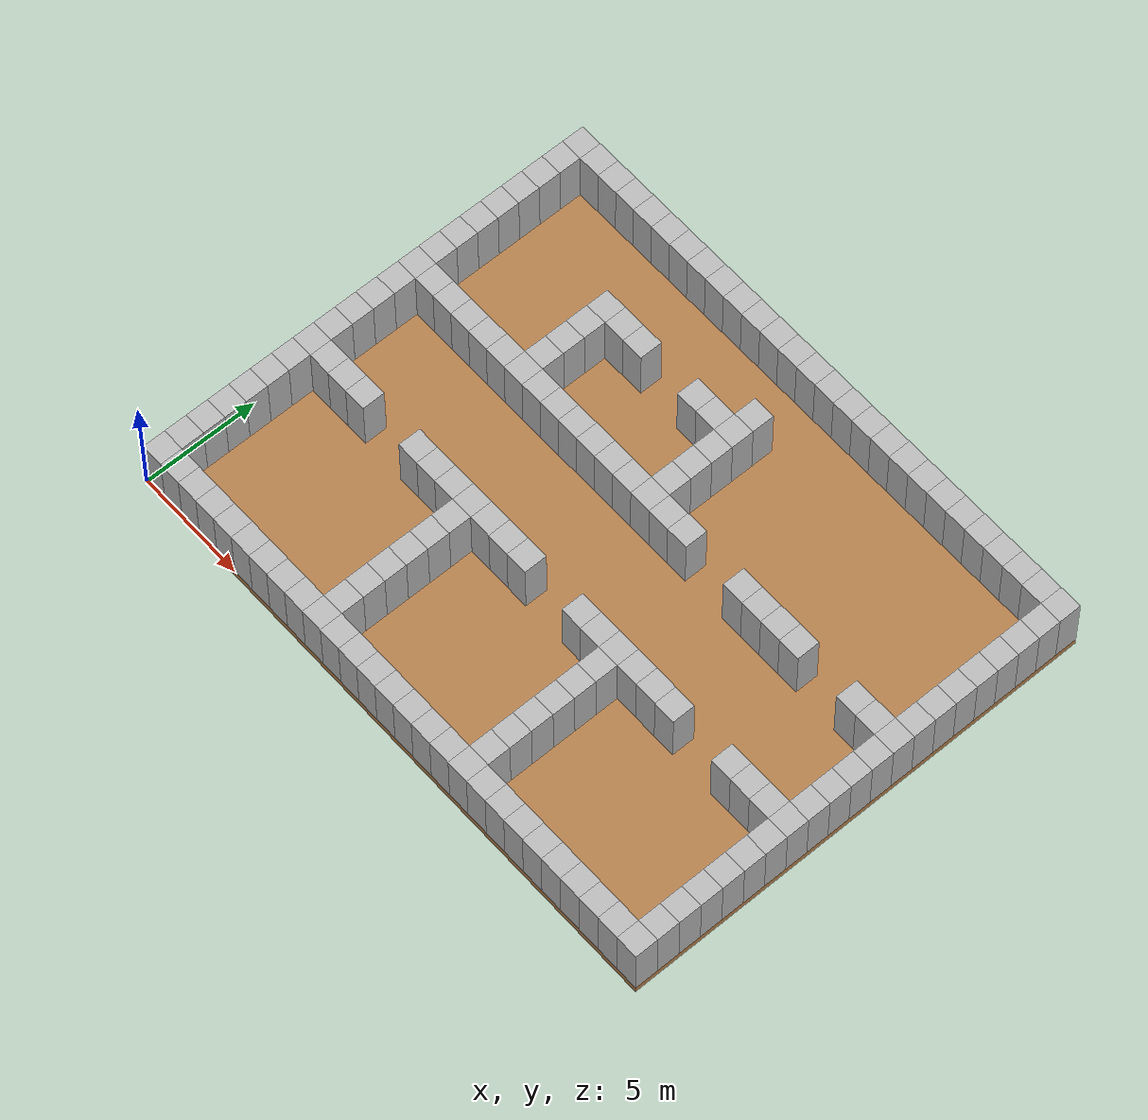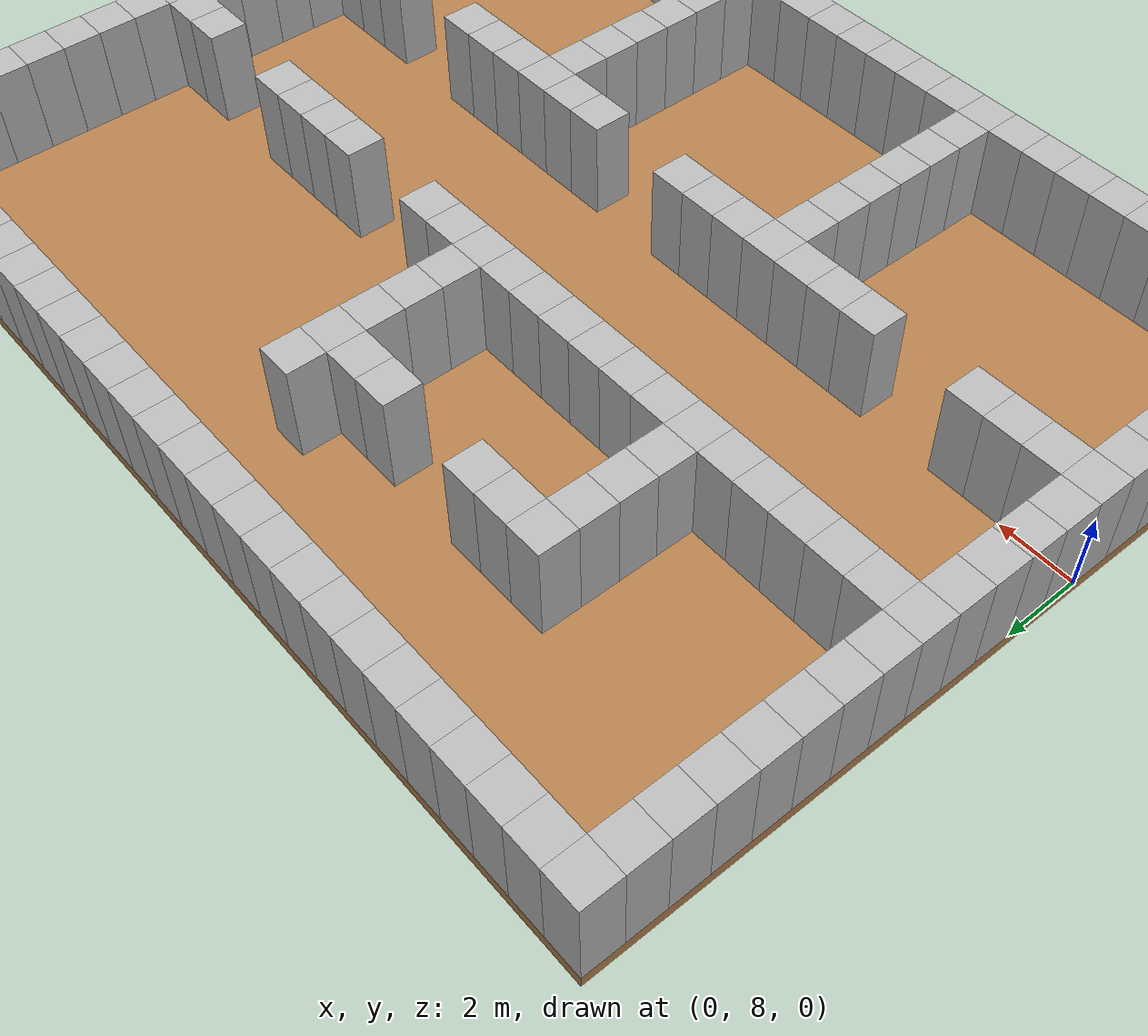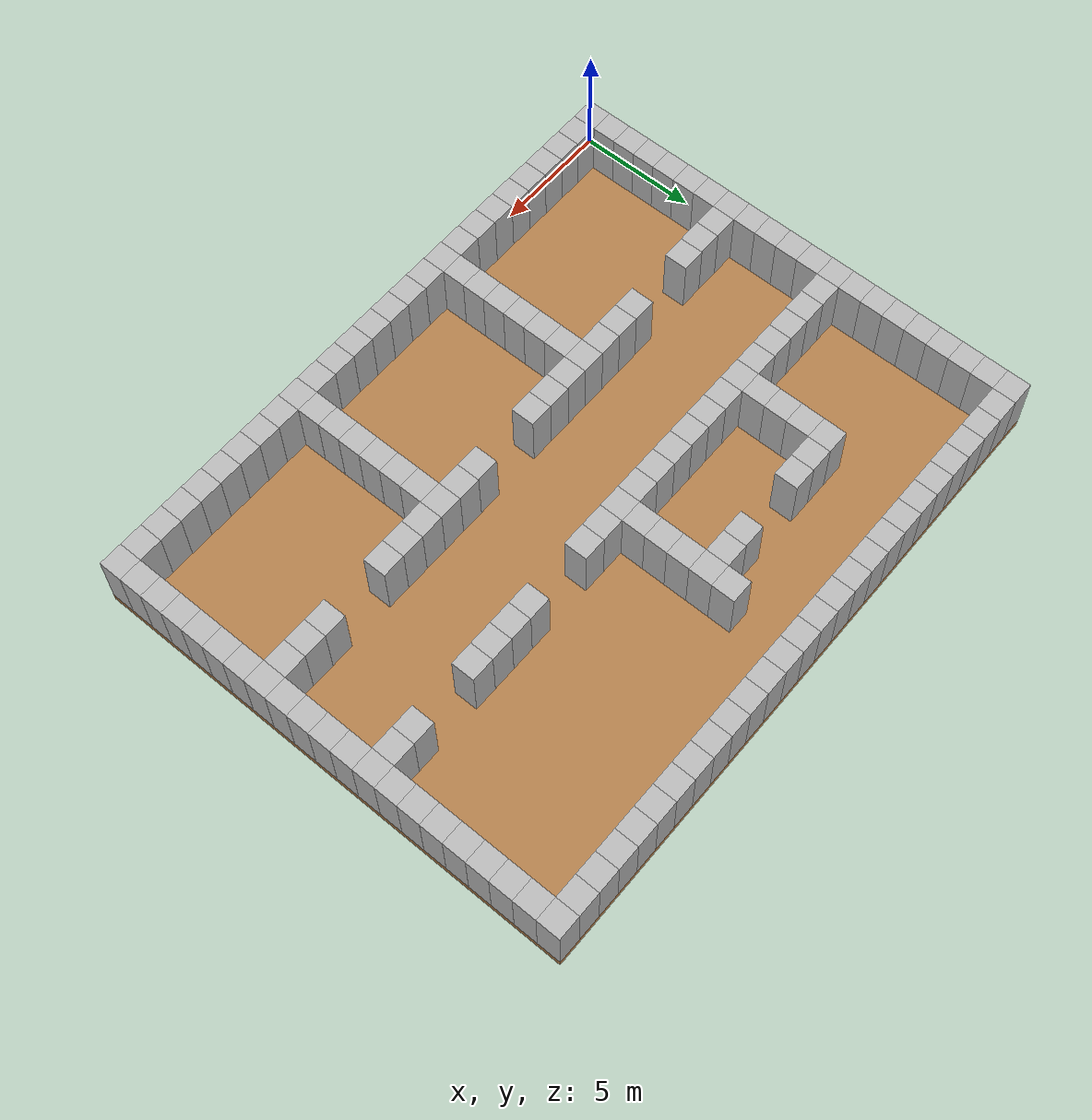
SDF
<sdf version="1.4">
 <world name="default">
  <light name="sun" type="directional">
   <diffuse>0.8 0.8 0.8 1</diffuse>
   <specular>0.1 0.1 0.1 1</specular>
   <attenuation>
    <range>1000</range>
    <constant>0.9</constant>
    <linear>0.01</linear>
    <quadratic>0.001</quadratic>
   </attenuation>
   <direction>-0.5 0.5 -1</direction>
  </light>
  <model name="floor">
   <pose>13.5 10.5 -0.15625 0 0 0</pose>
   <static>true</static>
   <link name="link">
    <collision name="collision"><geometry><box><size>27.0 21.0 0.3125</size></box></geometry></collision>
    <visual name="visual">
     <material>
      <script><uri>file://media/materials/scripts/Gazebo.material</uri><name>Gazebo/Wood</name></script>
     </material>
     <geometry><box><size>27.0 21.0 0.3125</size></box></geometry>
    </visual>
   </link>
  </model>
  <model name="box_0_0">
   <pose>0.5 0.5 1.25 0 0 0</pose>
   <static>true</static>
   <link name="link">
    <collision name="collision"><geometry><box><size>1.0 1.0 2.5</size></box></geometry></collision>
    <visual name="body_visual">
     <material>
      <script><uri>file://media/materials/scripts/repeated.material</uri><name>Repeated/seamless</name></script>
     </material>
     <geometry><box><size>1.0 1.0 2.5</size></box></geometry>
    </visual>
   </link>
  </model>
  <model name="box_0_1">
   <pose>0.5 1.5 1.25 0 0 0</pose>
   <static>true</static>
   <link name="link">
    <collision name="collision"><geometry><box><size>1.0 1.0 2.5</size></box></geometry></collision>
    <visual name="body_visual">
     <material>
      <script><uri>file://media/materials/scripts/repeated.material</uri><name>Repeated/seamless</name></script>
     </material>
     <geometry><box><size>1.0 1.0 2.5</size></box></geometry>
    </visual>
   </link>
  </model>
  <model name="box_0_2">
   <pose>0.5 2.5 1.25 0 0 0</pose>
   <static>true</static>
   <link name="link">
    <collision name="collision"><geometry><box><size>1.0 1.0 2.5</size></box></geometry></collision>
    <visual name="body_visual">
     <material>
      <script><uri>file://media/materials/scripts/repeated.material</uri><name>Repeated/seamless</name></script>
     </material>
     <geometry><box><size>1.0 1.0 2.5</size></box></geometry>
    </visual>
   </link>
  </model>
  <model name="box_0_3">
   <pose>0.5 3.5 1.25 0 0 0</pose>
   <static>true</static>
   <link name="link">
    <collision name="collision"><geometry><box><size>1.0 1.0 2.5</size></box></geometry></collision>
    <visual name="body_visual">
     <material>
      <script><uri>file://media/materials/scripts/repeated.material</uri><name>Repeated/seamless</name></script>
     </material>
     <geometry><box><size>1.0 1.0 2.5</size></box></geometry>
    </visual>
   </link>
  </model>
  <model name="box_0_4">
   <pose>0.5 4.5 1.25 0 0 0</pose>
   <static>true</static>
   <link name="link">
    <collision name="collision"><geometry><box><size>1.0 1.0 2.5</size></box></geometry></collision>
    <visual name="body_visual">
     <material>
      <script><uri>file://media/materials/scripts/repeated.material</uri><name>Repeated/seamless</name></script>
     </material>
     <geometry><box><size>1.0 1.0 2.5</size></box></geometry>
    </visual>
   </link>
  </model>
  <model name="box_0_5">
   <pose>0.5 5.5 1.25 0 0 0</pose>
   <static>true</static>
   <link name="link">
    <collision name="collision"><geometry><box><size>1.0 1.0 2.5</size></box></geometry></collision>
    <visual name="body_visual">
     <material>
      <script><uri>file://media/materials/scripts/repeated.material</uri><name>Repeated/seamless</name></script>
     </material>
     <geometry><box><size>1.0 1.0 2.5</size></box></geometry>
    </visual>
   </link>
  </model>
  <model name="box_0_6">
   <pose>0.5 6.5 1.25 0 0 0</pose>
   <static>true</static>
   <link name="link">
    <collision name="collision"><geometry><box><size>1.0 1.0 2.5</size></box></geometry></collision>
    <visual name="body_visual">
     <material>
      <script><uri>file://media/materials/scripts/repeated.material</uri><name>Repeated/seamless</name></script>
     </material>
     <geometry><box><size>1.0 1.0 2.5</size></box></geometry>
    </visual>
   </link>
  </model>
  <model name="box_0_7">
   <pose>0.5 7.5 1.25 0 0 0</pose>
   <static>true</static>
   <link name="link">
    <collision name="collision"><geometry><box><size>1.0 1.0 2.5</size></box></geometry></collision>
    <visual name="body_visual">
     <material>
      <script><uri>file://media/materials/scripts/repeated.material</uri><name>Repeated/seamless</name></script>
     </material>
     <geometry><box><size>1.0 1.0 2.5</size></box></geometry>
    </visual>
   </link>
  </model>
  <model name="box_0_8">
   <pose>0.5 8.5 1.25 0 0 0</pose>
   <static>true</static>
   <link name="link">
    <collision name="collision"><geometry><box><size>1.0 1.0 2.5</size></box></geometry></collision>
    <visual name="body_visual">
     <material>
      <script><uri>file://media/materials/scripts/repeated.material</uri><name>Repeated/seamless</name></script>
     </material>
     <geometry><box><size>1.0 1.0 2.5</size></box></geometry>
    </visual>
   </link>
  </model>
  <model name="box_0_9">
   <pose>0.5 9.5 1.25 0 0 0</pose>
   <static>true</static>
   <link name="link">
    <collision name="collision"><geometry><box><size>1.0 1.0 2.5</size></box></geometry></collision>
    <visual name="body_visual">
     <material>
      <script><uri>file://media/materials/scripts/repeated.material</uri><name>Repeated/seamless</name></script>
     </material>
     <geometry><box><size>1.0 1.0 2.5</size></box></geometry>
    </visual>
   </link>
  </model>
  <model name="box_0_10">
   <pose>0.5 10.5 1.25 0 0 0</pose>
   <static>true</static>
   <link name="link">
    <collision name="collision"><geometry><box><size>1.0 1.0 2.5</size></box></geometry></collision>
    <visual name="body_visual">
     <material>
      <script><uri>file://media/materials/scripts/repeated.material</uri><name>Repeated/seamless</name></script>
     </material>
     <geometry><box><size>1.0 1.0 2.5</size></box></geometry>
    </visual>
   </link>
  </model>
  <model name="box_0_11">
   <pose>0.5 11.5 1.25 0 0 0</pose>
   <static>true</static>
   <link name="link">
    <collision name="collision"><geometry><box><size>1.0 1.0 2.5</size></box></geometry></collision>
    <visual name="body_visual">
     <material>
      <script><uri>file://media/materials/scripts/repeated.material</uri><name>Repeated/seamless</name></script>
     </material>
     <geometry><box><size>1.0 1.0 2.5</size></box></geometry>
    </visual>
   </link>
  </model>
  <model name="box_0_12">
   <pose>0.5 12.5 1.25 0 0 0</pose>
   <static>true</static>
   <link name="link">
    <collision name="collision"><geometry><box><size>1.0 1.0 2.5</size></box></geometry></collision>
    <visual name="body_visual">
     <material>
      <script><uri>file://media/materials/scripts/repeated.material</uri><name>Repeated/seamless</name></script>
     </material>
     <geometry><box><size>1.0 1.0 2.5</size></box></geometry>
    </visual>
   </link>
  </model>
  <model name="box_0_13">
   <pose>0.5 13.5 1.25 0 0 0</pose>
   <static>true</static>
   <link name="link">
    <collision name="collision"><geometry><box><size>1.0 1.0 2.5</size></box></geometry></collision>
    <visual name="body_visual">
     <material>
      <script><uri>file://media/materials/scripts/repeated.material</uri><name>Repeated/seamless</name></script>
     </material>
     <geometry><box><size>1.0 1.0 2.5</size></box></geometry>
    </visual>
   </link>
  </model>
  <model name="box_0_14">
   <pose>0.5 14.5 1.25 0 0 0</pose>
   <static>true</static>
   <link name="link">
    <collision name="collision"><geometry><box><size>1.0 1.0 2.5</size></box></geometry></collision>
    <visual name="body_visual">
     <material>
      <script><uri>file://media/materials/scripts/repeated.material</uri><name>Repeated/seamless</name></script>
     </material>
     <geometry><box><size>1.0 1.0 2.5</size></box></geometry>
    </visual>
   </link>
  </model>
  <model name="box_0_15">
   <pose>0.5 15.5 1.25 0 0 0</pose>
   <static>true</static>
   <link name="link">
    <collision name="collision"><geometry><box><size>1.0 1.0 2.5</size></box></geometry></collision>
    <visual name="body_visual">
     <material>
      <script><uri>file://media/materials/scripts/repeated.material</uri><name>Repeated/seamless</name></script>
     </material>
     <geometry><box><size>1.0 1.0 2.5</size></box></geometry>
    </visual>
   </link>
  </model>
  <model name="box_0_16">
   <pose>0.5 16.5 1.25 0 0 0</pose>
   <static>true</static>
   <link name="link">
    <collision name="collision"><geometry><box><size>1.0 1.0 2.5</size></box></geometry></collision>
    <visual name="body_visual">
     <material>
      <script><uri>file://media/materials/scripts/repeated.material</uri><name>Repeated/seamless</name></script>
     </material>
     <geometry><box><size>1.0 1.0 2.5</size></box></geometry>
    </visual>
   </link>
  </model>
  <model name="box_0_17">
   <pose>0.5 17.5 1.25 0 0 0</pose>
   <static>true</static>
   <link name="link">
    <collision name="collision"><geometry><box><size>1.0 1.0 2.5</size></box></geometry></collision>
    <visual name="body_visual">
     <material>
      <script><uri>file://media/materials/scripts/repeated.material</uri><name>Repeated/seamless</name></script>
     </material>
     <geometry><box><size>1.0 1.0 2.5</size></box></geometry>
    </visual>
   </link>
  </model>
  <model name="box_0_18">
   <pose>0.5 18.5 1.25 0 0 0</pose>
   <static>true</static>
   <link name="link">
    <collision name="collision"><geometry><box><size>1.0 1.0 2.5</size></box></geometry></collision>
    <visual name="body_visual">
     <material>
      <script><uri>file://media/materials/scripts/repeated.material</uri><name>Repeated/seamless</name></script>
     </material>
     <geometry><box><size>1.0 1.0 2.5</size></box></geometry>
    </visual>
   </link>
  </model>
  <model name="box_0_19">
   <pose>0.5 19.5 1.25 0 0 0</pose>
   <static>true</static>
   <link name="link">
    <collision name="collision"><geometry><box><size>1.0 1.0 2.5</size></box></geometry></collision>
    <visual name="body_visual">
     <material>
      <script><uri>file://media/materials/scripts/repeated.material</uri><name>Repeated/seamless</name></script>
     </material>
     <geometry><box><size>1.0 1.0 2.5</size></box></geometry>
    </visual>
   </link>
  </model>
  <model name="box_0_20">
   <pose>0.5 20.5 1.25 0 0 0</pose>
   <static>true</static>
   <link name="link">
    <collision name="collision"><geometry><box><size>1.0 1.0 2.5</size></box></geometry></collision>
    <visual name="body_visual">
     <material>
      <script><uri>file://media/materials/scripts/repeated.material</uri><name>Repeated/seamless</name></script>
     </material>
     <geometry><box><size>1.0 1.0 2.5</size></box></geometry>
    </visual>
   </link>
  </model>
  <model name="box_1_0">
   <pose>1.5 0.5 1.25 0 0 0</pose>
   <static>true</static>
   <link name="link">
    <collision name="collision"><geometry><box><size>1.0 1.0 2.5</size></box></geometry></collision>
    <visual name="body_visual">
     <material>
      <script><uri>file://media/materials/scripts/repeated.material</uri><name>Repeated/seamless</name></script>
     </material>
     <geometry><box><size>1.0 1.0 2.5</size></box></geometry>
    </visual>
   </link>
  </model>
  <model name="box_1_7">
   <pose>1.5 7.5 1.25 0 0 0</pose>
   <static>true</static>
   <link name="link">
    <collision name="collision"><geometry><box><size>1.0 1.0 2.5</size></box></geometry></collision>
    <visual name="body_visual">
     <material>
      <script><uri>file://media/materials/scripts/repeated.material</uri><name>Repeated/seamless</name></script>
     </material>
     <geometry><box><size>1.0 1.0 2.5</size></box></geometry>
    </visual>
   </link>
  </model>
  <model name="box_1_12">
   <pose>1.5 12.5 1.25 0 0 0</pose>
   <static>true</static>
   <link name="link">
    <collision name="collision"><geometry><box><size>1.0 1.0 2.5</size></box></geometry></collision>
    <visual name="body_visual">
     <material>
      <script><uri>file://media/materials/scripts/repeated.material</uri><name>Repeated/seamless</name></script>
     </material>
     <geometry><box><size>1.0 1.0 2.5</size></box></geometry>
    </visual>
   </link>
  </model>
  <model name="box_1_20">
   <pose>1.5 20.5 1.25 0 0 0</pose>
   <static>true</static>
   <link name="link">
    <collision name="collision"><geometry><box><size>1.0 1.0 2.5</size></box></geometry></collision>
    <visual name="body_visual">
     <material>
      <script><uri>file://media/materials/scripts/repeated.material</uri><name>Repeated/seamless</name></script>
     </material>
     <geometry><box><size>1.0 1.0 2.5</size></box></geometry>
    </visual>
   </link>
  </model>
  <model name="box_2_0">
   <pose>2.5 0.5 1.25 0 0 0</pose>
   <static>true</static>
   <link name="link">
    <collision name="collision"><geometry><box><size>1.0 1.0 2.5</size></box></geometry></collision>
    <visual name="body_visual">
     <material>
      <script><uri>file://media/materials/scripts/repeated.material</uri><name>Repeated/seamless</name></script>
     </material>
     <geometry><box><size>1.0 1.0 2.5</size></box></geometry>
    </visual>
   </link>
  </model>
  <model name="box_2_7">
   <pose>2.5 7.5 1.25 0 0 0</pose>
   <static>true</static>
   <link name="link">
    <collision name="collision"><geometry><box><size>1.0 1.0 2.5</size></box></geometry></collision>
    <visual name="body_visual">
     <material>
      <script><uri>file://media/materials/scripts/repeated.material</uri><name>Repeated/seamless</name></script>
     </material>
     <geometry><box><size>1.0 1.0 2.5</size></box></geometry>
    </visual>
   </link>
  </model>
  <model name="box_2_12">
   <pose>2.5 12.5 1.25 0 0 0</pose>
   <static>true</static>
   <link name="link">
    <collision name="collision"><geometry><box><size>1.0 1.0 2.5</size></box></geometry></collision>
    <visual name="body_visual">
     <material>
      <script><uri>file://media/materials/scripts/repeated.material</uri><name>Repeated/seamless</name></script>
     </material>
     <geometry><box><size>1.0 1.0 2.5</size></box></geometry>
    </visual>
   </link>
  </model>
  <model name="box_2_20">
   <pose>2.5 20.5 1.25 0 0 0</pose>
   <static>true</static>
   <link name="link">
    <collision name="collision"><geometry><box><size>1.0 1.0 2.5</size></box></geometry></collision>
    <visual name="body_visual">
     <material>
      <script><uri>file://media/materials/scripts/repeated.material</uri><name>Repeated/seamless</name></script>
     </material>
     <geometry><box><size>1.0 1.0 2.5</size></box></geometry>
    </visual>
   </link>
  </model>
  <model name="box_3_0">
   <pose>3.5 0.5 1.25 0 0 0</pose>
   <static>true</static>
   <link name="link">
    <collision name="collision"><geometry><box><size>1.0 1.0 2.5</size></box></geometry></collision>
    <visual name="body_visual">
     <material>
      <script><uri>file://media/materials/scripts/repeated.material</uri><name>Repeated/seamless</name></script>
     </material>
     <geometry><box><size>1.0 1.0 2.5</size></box></geometry>
    </visual>
   </link>
  </model>
  <model name="box_3_7">
   <pose>3.5 7.5 1.25 0 0 0</pose>
   <static>true</static>
   <link name="link">
    <collision name="collision"><geometry><box><size>1.0 1.0 2.5</size></box></geometry></collision>
    <visual name="body_visual">
     <material>
      <script><uri>file://media/materials/scripts/repeated.material</uri><name>Repeated/seamless</name></script>
     </material>
     <geometry><box><size>1.0 1.0 2.5</size></box></geometry>
    </visual>
   </link>
  </model>
  <model name="box_3_12">
   <pose>3.5 12.5 1.25 0 0 0</pose>
   <static>true</static>
   <link name="link">
    <collision name="collision"><geometry><box><size>1.0 1.0 2.5</size></box></geometry></collision>
    <visual name="body_visual">
     <material>
      <script><uri>file://media/materials/scripts/repeated.material</uri><name>Repeated/seamless</name></script>
     </material>
     <geometry><box><size>1.0 1.0 2.5</size></box></geometry>
    </visual>
   </link>
  </model>
  <model name="box_3_20">
   <pose>3.5 20.5 1.25 0 0 0</pose>
   <static>true</static>
   <link name="link">
    <collision name="collision"><geometry><box><size>1.0 1.0 2.5</size></box></geometry></collision>
    <visual name="body_visual">
     <material>
      <script><uri>file://media/materials/scripts/repeated.material</uri><name>Repeated/seamless</name></script>
     </material>
     <geometry><box><size>1.0 1.0 2.5</size></box></geometry>
    </visual>
   </link>
  </model>
  <model name="box_4_0">
   <pose>4.5 0.5 1.25 0 0 0</pose>
   <static>true</static>
   <link name="link">
    <collision name="collision"><geometry><box><size>1.0 1.0 2.5</size></box></geometry></collision>
    <visual name="body_visual">
     <material>
      <script><uri>file://media/materials/scripts/repeated.material</uri><name>Repeated/seamless</name></script>
     </material>
     <geometry><box><size>1.0 1.0 2.5</size></box></geometry>
    </visual>
   </link>
  </model>
  <model name="box_4_12">
   <pose>4.5 12.5 1.25 0 0 0</pose>
   <static>true</static>
   <link name="link">
    <collision name="collision"><geometry><box><size>1.0 1.0 2.5</size></box></geometry></collision>
    <visual name="body_visual">
     <material>
      <script><uri>file://media/materials/scripts/repeated.material</uri><name>Repeated/seamless</name></script>
     </material>
     <geometry><box><size>1.0 1.0 2.5</size></box></geometry>
    </visual>
   </link>
  </model>
  <model name="box_4_20">
   <pose>4.5 20.5 1.25 0 0 0</pose>
   <static>true</static>
   <link name="link">
    <collision name="collision"><geometry><box><size>1.0 1.0 2.5</size></box></geometry></collision>
    <visual name="body_visual">
     <material>
      <script><uri>file://media/materials/scripts/repeated.material</uri><name>Repeated/seamless</name></script>
     </material>
     <geometry><box><size>1.0 1.0 2.5</size></box></geometry>
    </visual>
   </link>
  </model>
  <model name="box_5_0">
   <pose>5.5 0.5 1.25 0 0 0</pose>
   <static>true</static>
   <link name="link">
    <collision name="collision"><geometry><box><size>1.0 1.0 2.5</size></box></geometry></collision>
    <visual name="body_visual">
     <material>
      <script><uri>file://media/materials/scripts/repeated.material</uri><name>Repeated/seamless</name></script>
     </material>
     <geometry><box><size>1.0 1.0 2.5</size></box></geometry>
    </visual>
   </link>
  </model>
  <model name="box_5_12">
   <pose>5.5 12.5 1.25 0 0 0</pose>
   <static>true</static>
   <link name="link">
    <collision name="collision"><geometry><box><size>1.0 1.0 2.5</size></box></geometry></collision>
    <visual name="body_visual">
     <material>
      <script><uri>file://media/materials/scripts/repeated.material</uri><name>Repeated/seamless</name></script>
     </material>
     <geometry><box><size>1.0 1.0 2.5</size></box></geometry>
    </visual>
   </link>
  </model>
  <model name="box_5_20">
   <pose>5.5 20.5 1.25 0 0 0</pose>
   <static>true</static>
   <link name="link">
    <collision name="collision"><geometry><box><size>1.0 1.0 2.5</size></box></geometry></collision>
    <visual name="body_visual">
     <material>
      <script><uri>file://media/materials/scripts/repeated.material</uri><name>Repeated/seamless</name></script>
     </material>
     <geometry><box><size>1.0 1.0 2.5</size></box></geometry>
    </visual>
   </link>
  </model>
  <model name="box_6_0">
   <pose>6.5 0.5 1.25 0 0 0</pose>
   <static>true</static>
   <link name="link">
    <collision name="collision"><geometry><box><size>1.0 1.0 2.5</size></box></geometry></collision>
    <visual name="body_visual">
     <material>
      <script><uri>file://media/materials/scripts/repeated.material</uri><name>Repeated/seamless</name></script>
     </material>
     <geometry><box><size>1.0 1.0 2.5</size></box></geometry>
    </visual>
   </link>
  </model>
  <model name="box_6_7">
   <pose>6.5 7.5 1.25 0 0 0</pose>
   <static>true</static>
   <link name="link">
    <collision name="collision"><geometry><box><size>1.0 1.0 2.5</size></box></geometry></collision>
    <visual name="body_visual">
     <material>
      <script><uri>file://media/materials/scripts/repeated.material</uri><name>Repeated/seamless</name></script>
     </material>
     <geometry><box><size>1.0 1.0 2.5</size></box></geometry>
    </visual>
   </link>
  </model>
  <model name="box_6_12">
   <pose>6.5 12.5 1.25 0 0 0</pose>
   <static>true</static>
   <link name="link">
    <collision name="collision"><geometry><box><size>1.0 1.0 2.5</size></box></geometry></collision>
    <visual name="body_visual">
     <material>
      <script><uri>file://media/materials/scripts/repeated.material</uri><name>Repeated/seamless</name></script>
     </material>
     <geometry><box><size>1.0 1.0 2.5</size></box></geometry>
    </visual>
   </link>
  </model>
  <model name="box_6_13">
   <pose>6.5 13.5 1.25 0 0 0</pose>
   <static>true</static>
   <link name="link">
    <collision name="collision"><geometry><box><size>1.0 1.0 2.5</size></box></geometry></collision>
    <visual name="body_visual">
     <material>
      <script><uri>file://media/materials/scripts/repeated.material</uri><name>Repeated/seamless</name></script>
     </material>
     <geometry><box><size>1.0 1.0 2.5</size></box></geometry>
    </visual>
   </link>
  </model>
  <model name="box_6_14">
   <pose>6.5 14.5 1.25 0 0 0</pose>
   <static>true</static>
   <link name="link">
    <collision name="collision"><geometry><box><size>1.0 1.0 2.5</size></box></geometry></collision>
    <visual name="body_visual">
     <material>
      <script><uri>file://media/materials/scripts/repeated.material</uri><name>Repeated/seamless</name></script>
     </material>
     <geometry><box><size>1.0 1.0 2.5</size></box></geometry>
    </visual>
   </link>
  </model>
  <model name="box_6_15">
   <pose>6.5 15.5 1.25 0 0 0</pose>
   <static>true</static>
   <link name="link">
    <collision name="collision"><geometry><box><size>1.0 1.0 2.5</size></box></geometry></collision>
    <visual name="body_visual">
     <material>
      <script><uri>file://media/materials/scripts/repeated.material</uri><name>Repeated/seamless</name></script>
     </material>
     <geometry><box><size>1.0 1.0 2.5</size></box></geometry>
    </visual>
   </link>
  </model>
  <model name="box_6_16">
   <pose>6.5 16.5 1.25 0 0 0</pose>
   <static>true</static>
   <link name="link">
    <collision name="collision"><geometry><box><size>1.0 1.0 2.5</size></box></geometry></collision>
    <visual name="body_visual">
     <material>
      <script><uri>file://media/materials/scripts/repeated.material</uri><name>Repeated/seamless</name></script>
     </material>
     <geometry><box><size>1.0 1.0 2.5</size></box></geometry>
    </visual>
   </link>
  </model>
  <model name="box_6_20">
   <pose>6.5 20.5 1.25 0 0 0</pose>
   <static>true</static>
   <link name="link">
    <collision name="collision"><geometry><box><size>1.0 1.0 2.5</size></box></geometry></collision>
    <visual name="body_visual">
     <material>
      <script><uri>file://media/materials/scripts/repeated.material</uri><name>Repeated/seamless</name></script>
     </material>
     <geometry><box><size>1.0 1.0 2.5</size></box></geometry>
    </visual>
   </link>
  </model>
  <model name="box_7_0">
   <pose>7.5 0.5 1.25 0 0 0</pose>
   <static>true</static>
   <link name="link">
    <collision name="collision"><geometry><box><size>1.0 1.0 2.5</size></box></geometry></collision>
    <visual name="body_visual">
     <material>
      <script><uri>file://media/materials/scripts/repeated.material</uri><name>Repeated/seamless</name></script>
     </material>
     <geometry><box><size>1.0 1.0 2.5</size></box></geometry>
    </visual>
   </link>
  </model>
  <model name="box_7_7">
   <pose>7.5 7.5 1.25 0 0 0</pose>
   <static>true</static>
   <link name="link">
    <collision name="collision"><geometry><box><size>1.0 1.0 2.5</size></box></geometry></collision>
    <visual name="body_visual">
     <material>
      <script><uri>file://media/materials/scripts/repeated.material</uri><name>Repeated/seamless</name></script>
     </material>
     <geometry><box><size>1.0 1.0 2.5</size></box></geometry>
    </visual>
   </link>
  </model>
  <model name="box_7_12">
   <pose>7.5 12.5 1.25 0 0 0</pose>
   <static>true</static>
   <link name="link">
    <collision name="collision"><geometry><box><size>1.0 1.0 2.5</size></box></geometry></collision>
    <visual name="body_visual">
     <material>
      <script><uri>file://media/materials/scripts/repeated.material</uri><name>Repeated/seamless</name></script>
     </material>
     <geometry><box><size>1.0 1.0 2.5</size></box></geometry>
    </visual>
   </link>
  </model>
  <model name="box_7_16">
   <pose>7.5 16.5 1.25 0 0 0</pose>
   <static>true</static>
   <link name="link">
    <collision name="collision"><geometry><box><size>1.0 1.0 2.5</size></box></geometry></collision>
    <visual name="body_visual">
     <material>
      <script><uri>file://media/materials/scripts/repeated.material</uri><name>Repeated/seamless</name></script>
     </material>
     <geometry><box><size>1.0 1.0 2.5</size></box></geometry>
    </visual>
   </link>
  </model>
  <model name="box_7_20">
   <pose>7.5 20.5 1.25 0 0 0</pose>
   <static>true</static>
   <link name="link">
    <collision name="collision"><geometry><box><size>1.0 1.0 2.5</size></box></geometry></collision>
    <visual name="body_visual">
     <material>
      <script><uri>file://media/materials/scripts/repeated.material</uri><name>Repeated/seamless</name></script>
     </material>
     <geometry><box><size>1.0 1.0 2.5</size></box></geometry>
    </visual>
   </link>
  </model>
  <model name="box_8_0">
   <pose>8.5 0.5 1.25 0 0 0</pose>
   <static>true</static>
   <link name="link">
    <collision name="collision"><geometry><box><size>1.0 1.0 2.5</size></box></geometry></collision>
    <visual name="body_visual">
     <material>
      <script><uri>file://media/materials/scripts/repeated.material</uri><name>Repeated/seamless</name></script>
     </material>
     <geometry><box><size>1.0 1.0 2.5</size></box></geometry>
    </visual>
   </link>
  </model>
  <model name="box_8_7">
   <pose>8.5 7.5 1.25 0 0 0</pose>
   <static>true</static>
   <link name="link">
    <collision name="collision"><geometry><box><size>1.0 1.0 2.5</size></box></geometry></collision>
    <visual name="body_visual">
     <material>
      <script><uri>file://media/materials/scripts/repeated.material</uri><name>Repeated/seamless</name></script>
     </material>
     <geometry><box><size>1.0 1.0 2.5</size></box></geometry>
    </visual>
   </link>
  </model>
  <model name="box_8_12">
   <pose>8.5 12.5 1.25 0 0 0</pose>
   <static>true</static>
   <link name="link">
    <collision name="collision"><geometry><box><size>1.0 1.0 2.5</size></box></geometry></collision>
    <visual name="body_visual">
     <material>
      <script><uri>file://media/materials/scripts/repeated.material</uri><name>Repeated/seamless</name></script>
     </material>
     <geometry><box><size>1.0 1.0 2.5</size></box></geometry>
    </visual>
   </link>
  </model>
  <model name="box_8_16">
   <pose>8.5 16.5 1.25 0 0 0</pose>
   <static>true</static>
   <link name="link">
    <collision name="collision"><geometry><box><size>1.0 1.0 2.5</size></box></geometry></collision>
    <visual name="body_visual">
     <material>
      <script><uri>file://media/materials/scripts/repeated.material</uri><name>Repeated/seamless</name></script>
     </material>
     <geometry><box><size>1.0 1.0 2.5</size></box></geometry>
    </visual>
   </link>
  </model>
  <model name="box_8_20">
   <pose>8.5 20.5 1.25 0 0 0</pose>
   <static>true</static>
   <link name="link">
    <collision name="collision"><geometry><box><size>1.0 1.0 2.5</size></box></geometry></collision>
    <visual name="body_visual">
     <material>
      <script><uri>file://media/materials/scripts/repeated.material</uri><name>Repeated/seamless</name></script>
     </material>
     <geometry><box><size>1.0 1.0 2.5</size></box></geometry>
    </visual>
   </link>
  </model>
  <model name="box_9_0">
   <pose>9.5 0.5 1.25 0 0 0</pose>
   <static>true</static>
   <link name="link">
    <collision name="collision"><geometry><box><size>1.0 1.0 2.5</size></box></geometry></collision>
    <visual name="body_visual">
     <material>
      <script><uri>file://media/materials/scripts/repeated.material</uri><name>Repeated/seamless</name></script>
     </material>
     <geometry><box><size>1.0 1.0 2.5</size></box></geometry>
    </visual>
   </link>
  </model>
  <model name="box_9_1">
   <pose>9.5 1.5 1.25 0 0 0</pose>
   <static>true</static>
   <link name="link">
    <collision name="collision"><geometry><box><size>1.0 1.0 2.5</size></box></geometry></collision>
    <visual name="body_visual">
     <material>
      <script><uri>file://media/materials/scripts/repeated.material</uri><name>Repeated/seamless</name></script>
     </material>
     <geometry><box><size>1.0 1.0 2.5</size></box></geometry>
    </visual>
   </link>
  </model>
  <model name="box_9_2">
   <pose>9.5 2.5 1.25 0 0 0</pose>
   <static>true</static>
   <link name="link">
    <collision name="collision"><geometry><box><size>1.0 1.0 2.5</size></box></geometry></collision>
    <visual name="body_visual">
     <material>
      <script><uri>file://media/materials/scripts/repeated.material</uri><name>Repeated/seamless</name></script>
     </material>
     <geometry><box><size>1.0 1.0 2.5</size></box></geometry>
    </visual>
   </link>
  </model>
  <model name="box_9_3">
   <pose>9.5 3.5 1.25 0 0 0</pose>
   <static>true</static>
   <link name="link">
    <collision name="collision"><geometry><box><size>1.0 1.0 2.5</size></box></geometry></collision>
    <visual name="body_visual">
     <material>
      <script><uri>file://media/materials/scripts/repeated.material</uri><name>Repeated/seamless</name></script>
     </material>
     <geometry><box><size>1.0 1.0 2.5</size></box></geometry>
    </visual>
   </link>
  </model>
  <model name="box_9_4">
   <pose>9.5 4.5 1.25 0 0 0</pose>
   <static>true</static>
   <link name="link">
    <collision name="collision"><geometry><box><size>1.0 1.0 2.5</size></box></geometry></collision>
    <visual name="body_visual">
     <material>
      <script><uri>file://media/materials/scripts/repeated.material</uri><name>Repeated/seamless</name></script>
     </material>
     <geometry><box><size>1.0 1.0 2.5</size></box></geometry>
    </visual>
   </link>
  </model>
  <model name="box_9_5">
   <pose>9.5 5.5 1.25 0 0 0</pose>
   <static>true</static>
   <link name="link">
    <collision name="collision"><geometry><box><size>1.0 1.0 2.5</size></box></geometry></collision>
    <visual name="body_visual">
     <material>
      <script><uri>file://media/materials/scripts/repeated.material</uri><name>Repeated/seamless</name></script>
     </material>
     <geometry><box><size>1.0 1.0 2.5</size></box></geometry>
    </visual>
   </link>
  </model>
  <model name="box_9_6">
   <pose>9.5 6.5 1.25 0 0 0</pose>
   <static>true</static>
   <link name="link">
    <collision name="collision"><geometry><box><size>1.0 1.0 2.5</size></box></geometry></collision>
    <visual name="body_visual">
     <material>
      <script><uri>file://media/materials/scripts/repeated.material</uri><name>Repeated/seamless</name></script>
     </material>
     <geometry><box><size>1.0 1.0 2.5</size></box></geometry>
    </visual>
   </link>
  </model>
  <model name="box_9_7">
   <pose>9.5 7.5 1.25 0 0 0</pose>
   <static>true</static>
   <link name="link">
    <collision name="collision"><geometry><box><size>1.0 1.0 2.5</size></box></geometry></collision>
    <visual name="body_visual">
     <material>
      <script><uri>file://media/materials/scripts/repeated.material</uri><name>Repeated/seamless</name></script>
     </material>
     <geometry><box><size>1.0 1.0 2.5</size></box></geometry>
    </visual>
   </link>
  </model>
  <model name="box_9_12">
   <pose>9.5 12.5 1.25 0 0 0</pose>
   <static>true</static>
   <link name="link">
    <collision name="collision"><geometry><box><size>1.0 1.0 2.5</size></box></geometry></collision>
    <visual name="body_visual">
     <material>
      <script><uri>file://media/materials/scripts/repeated.material</uri><name>Repeated/seamless</name></script>
     </material>
     <geometry><box><size>1.0 1.0 2.5</size></box></geometry>
    </visual>
   </link>
  </model>
  <model name="box_9_20">
   <pose>9.5 20.5 1.25 0 0 0</pose>
   <static>true</static>
   <link name="link">
    <collision name="collision"><geometry><box><size>1.0 1.0 2.5</size></box></geometry></collision>
    <visual name="body_visual">
     <material>
      <script><uri>file://media/materials/scripts/repeated.material</uri><name>Repeated/seamless</name></script>
     </material>
     <geometry><box><size>1.0 1.0 2.5</size></box></geometry>
    </visual>
   </link>
  </model>
  <model name="box_10_0">
   <pose>10.5 0.5 1.25 0 0 0</pose>
   <static>true</static>
   <link name="link">
    <collision name="collision"><geometry><box><size>1.0 1.0 2.5</size></box></geometry></collision>
    <visual name="body_visual">
     <material>
      <script><uri>file://media/materials/scripts/repeated.material</uri><name>Repeated/seamless</name></script>
     </material>
     <geometry><box><size>1.0 1.0 2.5</size></box></geometry>
    </visual>
   </link>
  </model>
  <model name="box_10_7">
   <pose>10.5 7.5 1.25 0 0 0</pose>
   <static>true</static>
   <link name="link">
    <collision name="collision"><geometry><box><size>1.0 1.0 2.5</size></box></geometry></collision>
    <visual name="body_visual">
     <material>
      <script><uri>file://media/materials/scripts/repeated.material</uri><name>Repeated/seamless</name></script>
     </material>
     <geometry><box><size>1.0 1.0 2.5</size></box></geometry>
    </visual>
   </link>
  </model>
  <model name="box_10_12">
   <pose>10.5 12.5 1.25 0 0 0</pose>
   <static>true</static>
   <link name="link">
    <collision name="collision"><geometry><box><size>1.0 1.0 2.5</size></box></geometry></collision>
    <visual name="body_visual">
     <material>
      <script><uri>file://media/materials/scripts/repeated.material</uri><name>Repeated/seamless</name></script>
     </material>
     <geometry><box><size>1.0 1.0 2.5</size></box></geometry>
    </visual>
   </link>
  </model>
  <model name="box_10_20">
   <pose>10.5 20.5 1.25 0 0 0</pose>
   <static>true</static>
   <link name="link">
    <collision name="collision"><geometry><box><size>1.0 1.0 2.5</size></box></geometry></collision>
    <visual name="body_visual">
     <material>
      <script><uri>file://media/materials/scripts/repeated.material</uri><name>Repeated/seamless</name></script>
     </material>
     <geometry><box><size>1.0 1.0 2.5</size></box></geometry>
    </visual>
   </link>
  </model>
  <model name="box_11_0">
   <pose>11.5 0.5 1.25 0 0 0</pose>
   <static>true</static>
   <link name="link">
    <collision name="collision"><geometry><box><size>1.0 1.0 2.5</size></box></geometry></collision>
    <visual name="body_visual">
     <material>
      <script><uri>file://media/materials/scripts/repeated.material</uri><name>Repeated/seamless</name></script>
     </material>
     <geometry><box><size>1.0 1.0 2.5</size></box></geometry>
    </visual>
   </link>
  </model>
  <model name="box_11_7">
   <pose>11.5 7.5 1.25 0 0 0</pose>
   <static>true</static>
   <link name="link">
    <collision name="collision"><geometry><box><size>1.0 1.0 2.5</size></box></geometry></collision>
    <visual name="body_visual">
     <material>
      <script><uri>file://media/materials/scripts/repeated.material</uri><name>Repeated/seamless</name></script>
     </material>
     <geometry><box><size>1.0 1.0 2.5</size></box></geometry>
    </visual>
   </link>
  </model>
  <model name="box_11_12">
   <pose>11.5 12.5 1.25 0 0 0</pose>
   <static>true</static>
   <link name="link">
    <collision name="collision"><geometry><box><size>1.0 1.0 2.5</size></box></geometry></collision>
    <visual name="body_visual">
     <material>
      <script><uri>file://media/materials/scripts/repeated.material</uri><name>Repeated/seamless</name></script>
     </material>
     <geometry><box><size>1.0 1.0 2.5</size></box></geometry>
    </visual>
   </link>
  </model>
  <model name="box_11_16">
   <pose>11.5 16.5 1.25 0 0 0</pose>
   <static>true</static>
   <link name="link">
    <collision name="collision"><geometry><box><size>1.0 1.0 2.5</size></box></geometry></collision>
    <visual name="body_visual">
     <material>
      <script><uri>file://media/materials/scripts/repeated.material</uri><name>Repeated/seamless</name></script>
     </material>
     <geometry><box><size>1.0 1.0 2.5</size></box></geometry>
    </visual>
   </link>
  </model>
  <model name="box_11_20">
   <pose>11.5 20.5 1.25 0 0 0</pose>
   <static>true</static>
   <link name="link">
    <collision name="collision"><geometry><box><size>1.0 1.0 2.5</size></box></geometry></collision>
    <visual name="body_visual">
     <material>
      <script><uri>file://media/materials/scripts/repeated.material</uri><name>Repeated/seamless</name></script>
     </material>
     <geometry><box><size>1.0 1.0 2.5</size></box></geometry>
    </visual>
   </link>
  </model>
  <model name="box_12_0">
   <pose>12.5 0.5 1.25 0 0 0</pose>
   <static>true</static>
   <link name="link">
    <collision name="collision"><geometry><box><size>1.0 1.0 2.5</size></box></geometry></collision>
    <visual name="body_visual">
     <material>
      <script><uri>file://media/materials/scripts/repeated.material</uri><name>Repeated/seamless</name></script>
     </material>
     <geometry><box><size>1.0 1.0 2.5</size></box></geometry>
    </visual>
   </link>
  </model>
  <model name="box_12_7">
   <pose>12.5 7.5 1.25 0 0 0</pose>
   <static>true</static>
   <link name="link">
    <collision name="collision"><geometry><box><size>1.0 1.0 2.5</size></box></geometry></collision>
    <visual name="body_visual">
     <material>
      <script><uri>file://media/materials/scripts/repeated.material</uri><name>Repeated/seamless</name></script>
     </material>
     <geometry><box><size>1.0 1.0 2.5</size></box></geometry>
    </visual>
   </link>
  </model>
  <model name="box_12_12">
   <pose>12.5 12.5 1.25 0 0 0</pose>
   <static>true</static>
   <link name="link">
    <collision name="collision"><geometry><box><size>1.0 1.0 2.5</size></box></geometry></collision>
    <visual name="body_visual">
     <material>
      <script><uri>file://media/materials/scripts/repeated.material</uri><name>Repeated/seamless</name></script>
     </material>
     <geometry><box><size>1.0 1.0 2.5</size></box></geometry>
    </visual>
   </link>
  </model>
  <model name="box_12_16">
   <pose>12.5 16.5 1.25 0 0 0</pose>
   <static>true</static>
   <link name="link">
    <collision name="collision"><geometry><box><size>1.0 1.0 2.5</size></box></geometry></collision>
    <visual name="body_visual">
     <material>
      <script><uri>file://media/materials/scripts/repeated.material</uri><name>Repeated/seamless</name></script>
     </material>
     <geometry><box><size>1.0 1.0 2.5</size></box></geometry>
    </visual>
   </link>
  </model>
  <model name="box_12_20">
   <pose>12.5 20.5 1.25 0 0 0</pose>
   <static>true</static>
   <link name="link">
    <collision name="collision"><geometry><box><size>1.0 1.0 2.5</size></box></geometry></collision>
    <visual name="body_visual">
     <material>
      <script><uri>file://media/materials/scripts/repeated.material</uri><name>Repeated/seamless</name></script>
     </material>
     <geometry><box><size>1.0 1.0 2.5</size></box></geometry>
    </visual>
   </link>
  </model>
  <model name="box_13_0">
   <pose>13.5 0.5 1.25 0 0 0</pose>
   <static>true</static>
   <link name="link">
    <collision name="collision"><geometry><box><size>1.0 1.0 2.5</size></box></geometry></collision>
    <visual name="body_visual">
     <material>
      <script><uri>file://media/materials/scripts/repeated.material</uri><name>Repeated/seamless</name></script>
     </material>
     <geometry><box><size>1.0 1.0 2.5</size></box></geometry>
    </visual>
   </link>
  </model>
  <model name="box_13_12">
   <pose>13.5 12.5 1.25 0 0 0</pose>
   <static>true</static>
   <link name="link">
    <collision name="collision"><geometry><box><size>1.0 1.0 2.5</size></box></geometry></collision>
    <visual name="body_visual">
     <material>
      <script><uri>file://media/materials/scripts/repeated.material</uri><name>Repeated/seamless</name></script>
     </material>
     <geometry><box><size>1.0 1.0 2.5</size></box></geometry>
    </visual>
   </link>
  </model>
  <model name="box_13_13">
   <pose>13.5 13.5 1.25 0 0 0</pose>
   <static>true</static>
   <link name="link">
    <collision name="collision"><geometry><box><size>1.0 1.0 2.5</size></box></geometry></collision>
    <visual name="body_visual">
     <material>
      <script><uri>file://media/materials/scripts/repeated.material</uri><name>Repeated/seamless</name></script>
     </material>
     <geometry><box><size>1.0 1.0 2.5</size></box></geometry>
    </visual>
   </link>
  </model>
  <model name="box_13_14">
   <pose>13.5 14.5 1.25 0 0 0</pose>
   <static>true</static>
   <link name="link">
    <collision name="collision"><geometry><box><size>1.0 1.0 2.5</size></box></geometry></collision>
    <visual name="body_visual">
     <material>
      <script><uri>file://media/materials/scripts/repeated.material</uri><name>Repeated/seamless</name></script>
     </material>
     <geometry><box><size>1.0 1.0 2.5</size></box></geometry>
    </visual>
   </link>
  </model>
  <model name="box_13_15">
   <pose>13.5 15.5 1.25 0 0 0</pose>
   <static>true</static>
   <link name="link">
    <collision name="collision"><geometry><box><size>1.0 1.0 2.5</size></box></geometry></collision>
    <visual name="body_visual">
     <material>
      <script><uri>file://media/materials/scripts/repeated.material</uri><name>Repeated/seamless</name></script>
     </material>
     <geometry><box><size>1.0 1.0 2.5</size></box></geometry>
    </visual>
   </link>
  </model>
  <model name="box_13_16">
   <pose>13.5 16.5 1.25 0 0 0</pose>
   <static>true</static>
   <link name="link">
    <collision name="collision"><geometry><box><size>1.0 1.0 2.5</size></box></geometry></collision>
    <visual name="body_visual">
     <material>
      <script><uri>file://media/materials/scripts/repeated.material</uri><name>Repeated/seamless</name></script>
     </material>
     <geometry><box><size>1.0 1.0 2.5</size></box></geometry>
    </visual>
   </link>
  </model>
  <model name="box_13_17">
   <pose>13.5 17.5 1.25 0 0 0</pose>
   <static>true</static>
   <link name="link">
    <collision name="collision"><geometry><box><size>1.0 1.0 2.5</size></box></geometry></collision>
    <visual name="body_visual">
     <material>
      <script><uri>file://media/materials/scripts/repeated.material</uri><name>Repeated/seamless</name></script>
     </material>
     <geometry><box><size>1.0 1.0 2.5</size></box></geometry>
    </visual>
   </link>
  </model>
  <model name="box_13_20">
   <pose>13.5 20.5 1.25 0 0 0</pose>
   <static>true</static>
   <link name="link">
    <collision name="collision"><geometry><box><size>1.0 1.0 2.5</size></box></geometry></collision>
    <visual name="body_visual">
     <material>
      <script><uri>file://media/materials/scripts/repeated.material</uri><name>Repeated/seamless</name></script>
     </material>
     <geometry><box><size>1.0 1.0 2.5</size></box></geometry>
    </visual>
   </link>
  </model>
  <model name="box_14_0">
   <pose>14.5 0.5 1.25 0 0 0</pose>
   <static>true</static>
   <link name="link">
    <collision name="collision"><geometry><box><size>1.0 1.0 2.5</size></box></geometry></collision>
    <visual name="body_visual">
     <material>
      <script><uri>file://media/materials/scripts/repeated.material</uri><name>Repeated/seamless</name></script>
     </material>
     <geometry><box><size>1.0 1.0 2.5</size></box></geometry>
    </visual>
   </link>
  </model>
  <model name="box_14_12">
   <pose>14.5 12.5 1.25 0 0 0</pose>
   <static>true</static>
   <link name="link">
    <collision name="collision"><geometry><box><size>1.0 1.0 2.5</size></box></geometry></collision>
    <visual name="body_visual">
     <material>
      <script><uri>file://media/materials/scripts/repeated.material</uri><name>Repeated/seamless</name></script>
     </material>
     <geometry><box><size>1.0 1.0 2.5</size></box></geometry>
    </visual>
   </link>
  </model>
  <model name="box_14_20">
   <pose>14.5 20.5 1.25 0 0 0</pose>
   <static>true</static>
   <link name="link">
    <collision name="collision"><geometry><box><size>1.0 1.0 2.5</size></box></geometry></collision>
    <visual name="body_visual">
     <material>
      <script><uri>file://media/materials/scripts/repeated.material</uri><name>Repeated/seamless</name></script>
     </material>
     <geometry><box><size>1.0 1.0 2.5</size></box></geometry>
    </visual>
   </link>
  </model>
  <model name="box_15_0">
   <pose>15.5 0.5 1.25 0 0 0</pose>
   <static>true</static>
   <link name="link">
    <collision name="collision"><geometry><box><size>1.0 1.0 2.5</size></box></geometry></collision>
    <visual name="body_visual">
     <material>
      <script><uri>file://media/materials/scripts/repeated.material</uri><name>Repeated/seamless</name></script>
     </material>
     <geometry><box><size>1.0 1.0 2.5</size></box></geometry>
    </visual>
   </link>
  </model>
  <model name="box_15_7">
   <pose>15.5 7.5 1.25 0 0 0</pose>
   <static>true</static>
   <link name="link">
    <collision name="collision"><geometry><box><size>1.0 1.0 2.5</size></box></geometry></collision>
    <visual name="body_visual">
     <material>
      <script><uri>file://media/materials/scripts/repeated.material</uri><name>Repeated/seamless</name></script>
     </material>
     <geometry><box><size>1.0 1.0 2.5</size></box></geometry>
    </visual>
   </link>
  </model>
  <model name="box_15_12">
   <pose>15.5 12.5 1.25 0 0 0</pose>
   <static>true</static>
   <link name="link">
    <collision name="collision"><geometry><box><size>1.0 1.0 2.5</size></box></geometry></collision>
    <visual name="body_visual">
     <material>
      <script><uri>file://media/materials/scripts/repeated.material</uri><name>Repeated/seamless</name></script>
     </material>
     <geometry><box><size>1.0 1.0 2.5</size></box></geometry>
    </visual>
   </link>
  </model>
  <model name="box_15_20">
   <pose>15.5 20.5 1.25 0 0 0</pose>
   <static>true</static>
   <link name="link">
    <collision name="collision"><geometry><box><size>1.0 1.0 2.5</size></box></geometry></collision>
    <visual name="body_visual">
     <material>
      <script><uri>file://media/materials/scripts/repeated.material</uri><name>Repeated/seamless</name></script>
     </material>
     <geometry><box><size>1.0 1.0 2.5</size></box></geometry>
    </visual>
   </link>
  </model>
  <model name="box_16_0">
   <pose>16.5 0.5 1.25 0 0 0</pose>
   <static>true</static>
   <link name="link">
    <collision name="collision"><geometry><box><size>1.0 1.0 2.5</size></box></geometry></collision>
    <visual name="body_visual">
     <material>
      <script><uri>file://media/materials/scripts/repeated.material</uri><name>Repeated/seamless</name></script>
     </material>
     <geometry><box><size>1.0 1.0 2.5</size></box></geometry>
    </visual>
   </link>
  </model>
  <model name="box_16_7">
   <pose>16.5 7.5 1.25 0 0 0</pose>
   <static>true</static>
   <link name="link">
    <collision name="collision"><geometry><box><size>1.0 1.0 2.5</size></box></geometry></collision>
    <visual name="body_visual">
     <material>
      <script><uri>file://media/materials/scripts/repeated.material</uri><name>Repeated/seamless</name></script>
     </material>
     <geometry><box><size>1.0 1.0 2.5</size></box></geometry>
    </visual>
   </link>
  </model>
  <model name="box_16_20">
   <pose>16.5 20.5 1.25 0 0 0</pose>
   <static>true</static>
   <link name="link">
    <collision name="collision"><geometry><box><size>1.0 1.0 2.5</size></box></geometry></collision>
    <visual name="body_visual">
     <material>
      <script><uri>file://media/materials/scripts/repeated.material</uri><name>Repeated/seamless</name></script>
     </material>
     <geometry><box><size>1.0 1.0 2.5</size></box></geometry>
    </visual>
   </link>
  </model>
  <model name="box_17_0">
   <pose>17.5 0.5 1.25 0 0 0</pose>
   <static>true</static>
   <link name="link">
    <collision name="collision"><geometry><box><size>1.0 1.0 2.5</size></box></geometry></collision>
    <visual name="body_visual">
     <material>
      <script><uri>file://media/materials/scripts/repeated.material</uri><name>Repeated/seamless</name></script>
     </material>
     <geometry><box><size>1.0 1.0 2.5</size></box></geometry>
    </visual>
   </link>
  </model>
  <model name="box_17_1">
   <pose>17.5 1.5 1.25 0 0 0</pose>
   <static>true</static>
   <link name="link">
    <collision name="collision"><geometry><box><size>1.0 1.0 2.5</size></box></geometry></collision>
    <visual name="body_visual">
     <material>
      <script><uri>file://media/materials/scripts/repeated.material</uri><name>Repeated/seamless</name></script>
     </material>
     <geometry><box><size>1.0 1.0 2.5</size></box></geometry>
    </visual>
   </link>
  </model>
  <model name="box_17_2">
   <pose>17.5 2.5 1.25 0 0 0</pose>
   <static>true</static>
   <link name="link">
    <collision name="collision"><geometry><box><size>1.0 1.0 2.5</size></box></geometry></collision>
    <visual name="body_visual">
     <material>
      <script><uri>file://media/materials/scripts/repeated.material</uri><name>Repeated/seamless</name></script>
     </material>
     <geometry><box><size>1.0 1.0 2.5</size></box></geometry>
    </visual>
   </link>
  </model>
  <model name="box_17_3">
   <pose>17.5 3.5 1.25 0 0 0</pose>
   <static>true</static>
   <link name="link">
    <collision name="collision"><geometry><box><size>1.0 1.0 2.5</size></box></geometry></collision>
    <visual name="body_visual">
     <material>
      <script><uri>file://media/materials/scripts/repeated.material</uri><name>Repeated/seamless</name></script>
     </material>
     <geometry><box><size>1.0 1.0 2.5</size></box></geometry>
    </visual>
   </link>
  </model>
  <model name="box_17_4">
   <pose>17.5 4.5 1.25 0 0 0</pose>
   <static>true</static>
   <link name="link">
    <collision name="collision"><geometry><box><size>1.0 1.0 2.5</size></box></geometry></collision>
    <visual name="body_visual">
     <material>
      <script><uri>file://media/materials/scripts/repeated.material</uri><name>Repeated/seamless</name></script>
     </material>
     <geometry><box><size>1.0 1.0 2.5</size></box></geometry>
    </visual>
   </link>
  </model>
  <model name="box_17_5">
   <pose>17.5 5.5 1.25 0 0 0</pose>
   <static>true</static>
   <link name="link">
    <collision name="collision"><geometry><box><size>1.0 1.0 2.5</size></box></geometry></collision>
    <visual name="body_visual">
     <material>
      <script><uri>file://media/materials/scripts/repeated.material</uri><name>Repeated/seamless</name></script>
     </material>
     <geometry><box><size>1.0 1.0 2.5</size></box></geometry>
    </visual>
   </link>
  </model>
  <model name="box_17_6">
   <pose>17.5 6.5 1.25 0 0 0</pose>
   <static>true</static>
   <link name="link">
    <collision name="collision"><geometry><box><size>1.0 1.0 2.5</size></box></geometry></collision>
    <visual name="body_visual">
     <material>
      <script><uri>file://media/materials/scripts/repeated.material</uri><name>Repeated/seamless</name></script>
     </material>
     <geometry><box><size>1.0 1.0 2.5</size></box></geometry>
    </visual>
   </link>
  </model>
  <model name="box_17_7">
   <pose>17.5 7.5 1.25 0 0 0</pose>
   <static>true</static>
   <link name="link">
    <collision name="collision"><geometry><box><size>1.0 1.0 2.5</size></box></geometry></collision>
    <visual name="body_visual">
     <material>
      <script><uri>file://media/materials/scripts/repeated.material</uri><name>Repeated/seamless</name></script>
     </material>
     <geometry><box><size>1.0 1.0 2.5</size></box></geometry>
    </visual>
   </link>
  </model>
  <model name="box_17_20">
   <pose>17.5 20.5 1.25 0 0 0</pose>
   <static>true</static>
   <link name="link">
    <collision name="collision"><geometry><box><size>1.0 1.0 2.5</size></box></geometry></collision>
    <visual name="body_visual">
     <material>
      <script><uri>file://media/materials/scripts/repeated.material</uri><name>Repeated/seamless</name></script>
     </material>
     <geometry><box><size>1.0 1.0 2.5</size></box></geometry>
    </visual>
   </link>
  </model>
  <model name="box_18_0">
   <pose>18.5 0.5 1.25 0 0 0</pose>
   <static>true</static>
   <link name="link">
    <collision name="collision"><geometry><box><size>1.0 1.0 2.5</size></box></geometry></collision>
    <visual name="body_visual">
     <material>
      <script><uri>file://media/materials/scripts/repeated.material</uri><name>Repeated/seamless</name></script>
     </material>
     <geometry><box><size>1.0 1.0 2.5</size></box></geometry>
    </visual>
   </link>
  </model>
  <model name="box_18_7">
   <pose>18.5 7.5 1.25 0 0 0</pose>
   <static>true</static>
   <link name="link">
    <collision name="collision"><geometry><box><size>1.0 1.0 2.5</size></box></geometry></collision>
    <visual name="body_visual">
     <material>
      <script><uri>file://media/materials/scripts/repeated.material</uri><name>Repeated/seamless</name></script>
     </material>
     <geometry><box><size>1.0 1.0 2.5</size></box></geometry>
    </visual>
   </link>
  </model>
  <model name="box_18_12">
   <pose>18.5 12.5 1.25 0 0 0</pose>
   <static>true</static>
   <link name="link">
    <collision name="collision"><geometry><box><size>1.0 1.0 2.5</size></box></geometry></collision>
    <visual name="body_visual">
     <material>
      <script><uri>file://media/materials/scripts/repeated.material</uri><name>Repeated/seamless</name></script>
     </material>
     <geometry><box><size>1.0 1.0 2.5</size></box></geometry>
    </visual>
   </link>
  </model>
  <model name="box_18_20">
   <pose>18.5 20.5 1.25 0 0 0</pose>
   <static>true</static>
   <link name="link">
    <collision name="collision"><geometry><box><size>1.0 1.0 2.5</size></box></geometry></collision>
    <visual name="body_visual">
     <material>
      <script><uri>file://media/materials/scripts/repeated.material</uri><name>Repeated/seamless</name></script>
     </material>
     <geometry><box><size>1.0 1.0 2.5</size></box></geometry>
    </visual>
   </link>
  </model>
  <model name="box_19_0">
   <pose>19.5 0.5 1.25 0 0 0</pose>
   <static>true</static>
   <link name="link">
    <collision name="collision"><geometry><box><size>1.0 1.0 2.5</size></box></geometry></collision>
    <visual name="body_visual">
     <material>
      <script><uri>file://media/materials/scripts/repeated.material</uri><name>Repeated/seamless</name></script>
     </material>
     <geometry><box><size>1.0 1.0 2.5</size></box></geometry>
    </visual>
   </link>
  </model>
  <model name="box_19_7">
   <pose>19.5 7.5 1.25 0 0 0</pose>
   <static>true</static>
   <link name="link">
    <collision name="collision"><geometry><box><size>1.0 1.0 2.5</size></box></geometry></collision>
    <visual name="body_visual">
     <material>
      <script><uri>file://media/materials/scripts/repeated.material</uri><name>Repeated/seamless</name></script>
     </material>
     <geometry><box><size>1.0 1.0 2.5</size></box></geometry>
    </visual>
   </link>
  </model>
  <model name="box_19_12">
   <pose>19.5 12.5 1.25 0 0 0</pose>
   <static>true</static>
   <link name="link">
    <collision name="collision"><geometry><box><size>1.0 1.0 2.5</size></box></geometry></collision>
    <visual name="body_visual">
     <material>
      <script><uri>file://media/materials/scripts/repeated.material</uri><name>Repeated/seamless</name></script>
     </material>
     <geometry><box><size>1.0 1.0 2.5</size></box></geometry>
    </visual>
   </link>
  </model>
  <model name="box_19_20">
   <pose>19.5 20.5 1.25 0 0 0</pose>
   <static>true</static>
   <link name="link">
    <collision name="collision"><geometry><box><size>1.0 1.0 2.5</size></box></geometry></collision>
    <visual name="body_visual">
     <material>
      <script><uri>file://media/materials/scripts/repeated.material</uri><name>Repeated/seamless</name></script>
     </material>
     <geometry><box><size>1.0 1.0 2.5</size></box></geometry>
    </visual>
   </link>
  </model>
  <model name="box_20_0">
   <pose>20.5 0.5 1.25 0 0 0</pose>
   <static>true</static>
   <link name="link">
    <collision name="collision"><geometry><box><size>1.0 1.0 2.5</size></box></geometry></collision>
    <visual name="body_visual">
     <material>
      <script><uri>file://media/materials/scripts/repeated.material</uri><name>Repeated/seamless</name></script>
     </material>
     <geometry><box><size>1.0 1.0 2.5</size></box></geometry>
    </visual>
   </link>
  </model>
  <model name="box_20_7">
   <pose>20.5 7.5 1.25 0 0 0</pose>
   <static>true</static>
   <link name="link">
    <collision name="collision"><geometry><box><size>1.0 1.0 2.5</size></box></geometry></collision>
    <visual name="body_visual">
     <material>
      <script><uri>file://media/materials/scripts/repeated.material</uri><name>Repeated/seamless</name></script>
     </material>
     <geometry><box><size>1.0 1.0 2.5</size></box></geometry>
    </visual>
   </link>
  </model>
  <model name="box_20_12">
   <pose>20.5 12.5 1.25 0 0 0</pose>
   <static>true</static>
   <link name="link">
    <collision name="collision"><geometry><box><size>1.0 1.0 2.5</size></box></geometry></collision>
    <visual name="body_visual">
     <material>
      <script><uri>file://media/materials/scripts/repeated.material</uri><name>Repeated/seamless</name></script>
     </material>
     <geometry><box><size>1.0 1.0 2.5</size></box></geometry>
    </visual>
   </link>
  </model>
  <model name="box_20_20">
   <pose>20.5 20.5 1.25 0 0 0</pose>
   <static>true</static>
   <link name="link">
    <collision name="collision"><geometry><box><size>1.0 1.0 2.5</size></box></geometry></collision>
    <visual name="body_visual">
     <material>
      <script><uri>file://media/materials/scripts/repeated.material</uri><name>Repeated/seamless</name></script>
     </material>
     <geometry><box><size>1.0 1.0 2.5</size></box></geometry>
    </visual>
   </link>
  </model>
  <model name="box_21_0">
   <pose>21.5 0.5 1.25 0 0 0</pose>
   <static>true</static>
   <link name="link">
    <collision name="collision"><geometry><box><size>1.0 1.0 2.5</size></box></geometry></collision>
    <visual name="body_visual">
     <material>
      <script><uri>file://media/materials/scripts/repeated.material</uri><name>Repeated/seamless</name></script>
     </material>
     <geometry><box><size>1.0 1.0 2.5</size></box></geometry>
    </visual>
   </link>
  </model>
  <model name="box_21_12">
   <pose>21.5 12.5 1.25 0 0 0</pose>
   <static>true</static>
   <link name="link">
    <collision name="collision"><geometry><box><size>1.0 1.0 2.5</size></box></geometry></collision>
    <visual name="body_visual">
     <material>
      <script><uri>file://media/materials/scripts/repeated.material</uri><name>Repeated/seamless</name></script>
     </material>
     <geometry><box><size>1.0 1.0 2.5</size></box></geometry>
    </visual>
   </link>
  </model>
  <model name="box_21_20">
   <pose>21.5 20.5 1.25 0 0 0</pose>
   <static>true</static>
   <link name="link">
    <collision name="collision"><geometry><box><size>1.0 1.0 2.5</size></box></geometry></collision>
    <visual name="body_visual">
     <material>
      <script><uri>file://media/materials/scripts/repeated.material</uri><name>Repeated/seamless</name></script>
     </material>
     <geometry><box><size>1.0 1.0 2.5</size></box></geometry>
    </visual>
   </link>
  </model>
  <model name="box_22_0">
   <pose>22.5 0.5 1.25 0 0 0</pose>
   <static>true</static>
   <link name="link">
    <collision name="collision"><geometry><box><size>1.0 1.0 2.5</size></box></geometry></collision>
    <visual name="body_visual">
     <material>
      <script><uri>file://media/materials/scripts/repeated.material</uri><name>Repeated/seamless</name></script>
     </material>
     <geometry><box><size>1.0 1.0 2.5</size></box></geometry>
    </visual>
   </link>
  </model>
  <model name="box_22_20">
   <pose>22.5 20.5 1.25 0 0 0</pose>
   <static>true</static>
   <link name="link">
    <collision name="collision"><geometry><box><size>1.0 1.0 2.5</size></box></geometry></collision>
    <visual name="body_visual">
     <material>
      <script><uri>file://media/materials/scripts/repeated.material</uri><name>Repeated/seamless</name></script>
     </material>
     <geometry><box><size>1.0 1.0 2.5</size></box></geometry>
    </visual>
   </link>
  </model>
  <model name="box_23_0">
   <pose>23.5 0.5 1.25 0 0 0</pose>
   <static>true</static>
   <link name="link">
    <collision name="collision"><geometry><box><size>1.0 1.0 2.5</size></box></geometry></collision>
    <visual name="body_visual">
     <material>
      <script><uri>file://media/materials/scripts/repeated.material</uri><name>Repeated/seamless</name></script>
     </material>
     <geometry><box><size>1.0 1.0 2.5</size></box></geometry>
    </visual>
   </link>
  </model>
  <model name="box_23_7">
   <pose>23.5 7.5 1.25 0 0 0</pose>
   <static>true</static>
   <link name="link">
    <collision name="collision"><geometry><box><size>1.0 1.0 2.5</size></box></geometry></collision>
    <visual name="body_visual">
     <material>
      <script><uri>file://media/materials/scripts/repeated.material</uri><name>Repeated/seamless</name></script>
     </material>
     <geometry><box><size>1.0 1.0 2.5</size></box></geometry>
    </visual>
   </link>
  </model>
  <model name="box_23_20">
   <pose>23.5 20.5 1.25 0 0 0</pose>
   <static>true</static>
   <link name="link">
    <collision name="collision"><geometry><box><size>1.0 1.0 2.5</size></box></geometry></collision>
    <visual name="body_visual">
     <material>
      <script><uri>file://media/materials/scripts/repeated.material</uri><name>Repeated/seamless</name></script>
     </material>
     <geometry><box><size>1.0 1.0 2.5</size></box></geometry>
    </visual>
   </link>
  </model>
  <model name="box_24_0">
   <pose>24.5 0.5 1.25 0 0 0</pose>
   <static>true</static>
   <link name="link">
    <collision name="collision"><geometry><box><size>1.0 1.0 2.5</size></box></geometry></collision>
    <visual name="body_visual">
     <material>
      <script><uri>file://media/materials/scripts/repeated.material</uri><name>Repeated/seamless</name></script>
     </material>
     <geometry><box><size>1.0 1.0 2.5</size></box></geometry>
    </visual>
   </link>
  </model>
  <model name="box_24_7">
   <pose>24.5 7.5 1.25 0 0 0</pose>
   <static>true</static>
   <link name="link">
    <collision name="collision"><geometry><box><size>1.0 1.0 2.5</size></box></geometry></collision>
    <visual name="body_visual">
     <material>
      <script><uri>file://media/materials/scripts/repeated.material</uri><name>Repeated/seamless</name></script>
     </material>
     <geometry><box><size>1.0 1.0 2.5</size></box></geometry>
    </visual>
   </link>
  </model>
  <model name="box_24_12">
   <pose>24.5 12.5 1.25 0 0 0</pose>
   <static>true</static>
   <link name="link">
    <collision name="collision"><geometry><box><size>1.0 1.0 2.5</size></box></geometry></collision>
    <visual name="body_visual">
     <material>
      <script><uri>file://media/materials/scripts/repeated.material</uri><name>Repeated/seamless</name></script>
     </material>
     <geometry><box><size>1.0 1.0 2.5</size></box></geometry>
    </visual>
   </link>
  </model>
  <model name="box_24_20">
   <pose>24.5 20.5 1.25 0 0 0</pose>
   <static>true</static>
   <link name="link">
    <collision name="collision"><geometry><box><size>1.0 1.0 2.5</size></box></geometry></collision>
    <visual name="body_visual">
     <material>
      <script><uri>file://media/materials/scripts/repeated.material</uri><name>Repeated/seamless</name></script>
     </material>
     <geometry><box><size>1.0 1.0 2.5</size></box></geometry>
    </visual>
   </link>
  </model>
  <model name="box_25_0">
   <pose>25.5 0.5 1.25 0 0 0</pose>
   <static>true</static>
   <link name="link">
    <collision name="collision"><geometry><box><size>1.0 1.0 2.5</size></box></geometry></collision>
    <visual name="body_visual">
     <material>
      <script><uri>file://media/materials/scripts/repeated.material</uri><name>Repeated/seamless</name></script>
     </material>
     <geometry><box><size>1.0 1.0 2.5</size></box></geometry>
    </visual>
   </link>
  </model>
  <model name="box_25_7">
   <pose>25.5 7.5 1.25 0 0 0</pose>
   <static>true</static>
   <link name="link">
    <collision name="collision"><geometry><box><size>1.0 1.0 2.5</size></box></geometry></collision>
    <visual name="body_visual">
     <material>
      <script><uri>file://media/materials/scripts/repeated.material</uri><name>Repeated/seamless</name></script>
     </material>
     <geometry><box><size>1.0 1.0 2.5</size></box></geometry>
    </visual>
   </link>
  </model>
  <model name="box_25_12">
   <pose>25.5 12.5 1.25 0 0 0</pose>
   <static>true</static>
   <link name="link">
    <collision name="collision"><geometry><box><size>1.0 1.0 2.5</size></box></geometry></collision>
    <visual name="body_visual">
     <material>
      <script><uri>file://media/materials/scripts/repeated.material</uri><name>Repeated/seamless</name></script>
     </material>
     <geometry><box><size>1.0 1.0 2.5</size></box></geometry>
    </visual>
   </link>
  </model>
  <model name="box_25_20">
   <pose>25.5 20.5 1.25 0 0 0</pose>
   <static>true</static>
   <link name="link">
    <collision name="collision"><geometry><box><size>1.0 1.0 2.5</size></box></geometry></collision>
    <visual name="body_visual">
     <material>
      <script><uri>file://media/materials/scripts/repeated.material</uri><name>Repeated/seamless</name></script>
     </material>
     <geometry><box><size>1.0 1.0 2.5</size></box></geometry>
    </visual>
   </link>
  </model>
  <model name="box_26_0">
   <pose>26.5 0.5 1.25 0 0 0</pose>
   <static>true</static>
   <link name="link">
    <collision name="collision"><geometry><box><size>1.0 1.0 2.5</size></box></geometry></collision>
    <visual name="body_visual">
     <material>
      <script><uri>file://media/materials/scripts/repeated.material</uri><name>Repeated/seamless</name></script>
     </material>
     <geometry><box><size>1.0 1.0 2.5</size></box></geometry>
    </visual>
   </link>
  </model>
  <model name="box_26_1">
   <pose>26.5 1.5 1.25 0 0 0</pose>
   <static>true</static>
   <link name="link">
    <collision name="collision"><geometry><box><size>1.0 1.0 2.5</size></box></geometry></collision>
    <visual name="body_visual">
     <material>
      <script><uri>file://media/materials/scripts/repeated.material</uri><name>Repeated/seamless</name></script>
     </material>
     <geometry><box><size>1.0 1.0 2.5</size></box></geometry>
    </visual>
   </link>
  </model>
  <model name="box_26_2">
   <pose>26.5 2.5 1.25 0 0 0</pose>
   <static>true</static>
   <link name="link">
    <collision name="collision"><geometry><box><size>1.0 1.0 2.5</size></box></geometry></collision>
    <visual name="body_visual">
     <material>
      <script><uri>file://media/materials/scripts/repeated.material</uri><name>Repeated/seamless</name></script>
     </material>
     <geometry><box><size>1.0 1.0 2.5</size></box></geometry>
    </visual>
   </link>
  </model>
  <model name="box_26_3">
   <pose>26.5 3.5 1.25 0 0 0</pose>
   <static>true</static>
   <link name="link">
    <collision name="collision"><geometry><box><size>1.0 1.0 2.5</size></box></geometry></collision>
    <visual name="body_visual">
     <material>
      <script><uri>file://media/materials/scripts/repeated.material</uri><name>Repeated/seamless</name></script>
     </material>
     <geometry><box><size>1.0 1.0 2.5</size></box></geometry>
    </visual>
   </link>
  </model>
  <model name="box_26_4">
   <pose>26.5 4.5 1.25 0 0 0</pose>
   <static>true</static>
   <link name="link">
    <collision name="collision"><geometry><box><size>1.0 1.0 2.5</size></box></geometry></collision>
    <visual name="body_visual">
     <material>
      <script><uri>file://media/materials/scripts/repeated.material</uri><name>Repeated/seamless</name></script>
     </material>
     <geometry><box><size>1.0 1.0 2.5</size></box></geometry>
    </visual>
   </link>
  </model>
  <model name="box_26_5">
   <pose>26.5 5.5 1.25 0 0 0</pose>
   <static>true</static>
   <link name="link">
    <collision name="collision"><geometry><box><size>1.0 1.0 2.5</size></box></geometry></collision>
    <visual name="body_visual">
     <material>
      <script><uri>file://media/materials/scripts/repeated.material</uri><name>Repeated/seamless</name></script>
     </material>
     <geometry><box><size>1.0 1.0 2.5</size></box></geometry>
    </visual>
   </link>
  </model>
  <model name="box_26_6">
   <pose>26.5 6.5 1.25 0 0 0</pose>
   <static>true</static>
   <link name="link">
    <collision name="collision"><geometry><box><size>1.0 1.0 2.5</size></box></geometry></collision>
    <visual name="body_visual">
     <material>
      <script><uri>file://media/materials/scripts/repeated.material</uri><name>Repeated/seamless</name></script>
     </material>
     <geometry><box><size>1.0 1.0 2.5</size></box></geometry>
    </visual>
   </link>
  </model>
  <model name="box_26_7">
   <pose>26.5 7.5 1.25 0 0 0</pose>
   <static>true</static>
   <link name="link">
    <collision name="collision"><geometry><box><size>1.0 1.0 2.5</size></box></geometry></collision>
    <visual name="body_visual">
     <material>
      <script><uri>file://media/materials/scripts/repeated.material</uri><name>Repeated/seamless</name></script>
     </material>
     <geometry><box><size>1.0 1.0 2.5</size></box></geometry>
    </visual>
   </link>
  </model>
  <model name="box_26_8">
   <pose>26.5 8.5 1.25 0 0 0</pose>
   <static>true</static>
   <link name="link">
    <collision name="collision"><geometry><box><size>1.0 1.0 2.5</size></box></geometry></collision>
    <visual name="body_visual">
     <material>
      <script><uri>file://media/materials/scripts/repeated.material</uri><name>Repeated/seamless</name></script>
     </material>
     <geometry><box><size>1.0 1.0 2.5</size></box></geometry>
    </visual>
   </link>
  </model>
  <model name="box_26_9">
   <pose>26.5 9.5 1.25 0 0 0</pose>
   <static>true</static>
   <link name="link">
    <collision name="collision"><geometry><box><size>1.0 1.0 2.5</size></box></geometry></collision>
    <visual name="body_visual">
     <material>
      <script><uri>file://media/materials/scripts/repeated.material</uri><name>Repeated/seamless</name></script>
     </material>
     <geometry><box><size>1.0 1.0 2.5</size></box></geometry>
    </visual>
   </link>
  </model>
  <model name="box_26_10">
   <pose>26.5 10.5 1.25 0 0 0</pose>
   <static>true</static>
   <link name="link">
    <collision name="collision"><geometry><box><size>1.0 1.0 2.5</size></box></geometry></collision>
    <visual name="body_visual">
     <material>
      <script><uri>file://media/materials/scripts/repeated.material</uri><name>Repeated/seamless</name></script>
     </material>
     <geometry><box><size>1.0 1.0 2.5</size></box></geometry>
    </visual>
   </link>
  </model>
  <model name="box_26_11">
   <pose>26.5 11.5 1.25 0 0 0</pose>
   <static>true</static>
   <link name="link">
    <collision name="collision"><geometry><box><size>1.0 1.0 2.5</size></box></geometry></collision>
    <visual name="body_visual">
     <material>
      <script><uri>file://media/materials/scripts/repeated.material</uri><name>Repeated/seamless</name></script>
     </material>
     <geometry><box><size>1.0 1.0 2.5</size></box></geometry>
    </visual>
   </link>
  </model>
  <model name="box_26_12">
   <pose>26.5 12.5 1.25 0 0 0</pose>
   <static>true</static>
   <link name="link">
    <collision name="collision"><geometry><box><size>1.0 1.0 2.5</size></box></geometry></collision>
    <visual name="body_visual">
     <material>
      <script><uri>file://media/materials/scripts/repeated.material</uri><name>Repeated/seamless</name></script>
     </material>
     <geometry><box><size>1.0 1.0 2.5</size></box></geometry>
    </visual>
   </link>
  </model>
  <model name="box_26_13">
   <pose>26.5 13.5 1.25 0 0 0</pose>
   <static>true</static>
   <link name="link">
    <collision name="collision"><geometry><box><size>1.0 1.0 2.5</size></box></geometry></collision>
    <visual name="body_visual">
     <material>
      <script><uri>file://media/materials/scripts/repeated.material</uri><name>Repeated/seamless</name></script>
     </material>
     <geometry><box><size>1.0 1.0 2.5</size></box></geometry>
    </visual>
   </link>
  </model>
  <model name="box_26_14">
   <pose>26.5 14.5 1.25 0 0 0</pose>
   <static>true</static>
   <link name="link">
    <collision name="collision"><geometry><box><size>1.0 1.0 2.5</size></box></geometry></collision>
    <visual name="body_visual">
     <material>
      <script><uri>file://media/materials/scripts/repeated.material</uri><name>Repeated/seamless</name></script>
     </material>
     <geometry><box><size>1.0 1.0 2.5</size></box></geometry>
    </visual>
   </link>
  </model>
  <model name="box_26_15">
   <pose>26.5 15.5 1.25 0 0 0</pose>
   <static>true</static>
   <link name="link">
    <collision name="collision"><geometry><box><size>1.0 1.0 2.5</size></box></geometry></collision>
    <visual name="body_visual">
     <material>
      <script><uri>file://media/materials/scripts/repeated.material</uri><name>Repeated/seamless</name></script>
     </material>
     <geometry><box><size>1.0 1.0 2.5</size></box></geometry>
    </visual>
   </link>
  </model>
  <model name="box_26_16">
   <pose>26.5 16.5 1.25 0 0 0</pose>
   <static>true</static>
   <link name="link">
    <collision name="collision"><geometry><box><size>1.0 1.0 2.5</size></box></geometry></collision>
    <visual name="body_visual">
     <material>
      <script><uri>file://media/materials/scripts/repeated.material</uri><name>Repeated/seamless</name></script>
     </material>
     <geometry><box><size>1.0 1.0 2.5</size></box></geometry>
    </visual>
   </link>
  </model>
  <model name="box_26_17">
   <pose>26.5 17.5 1.25 0 0 0</pose>
   <static>true</static>
   <link name="link">
    <collision name="collision"><geometry><box><size>1.0 1.0 2.5</size></box></geometry></collision>
    <visual name="body_visual">
     <material>
      <script><uri>file://media/materials/scripts/repeated.material</uri><name>Repeated/seamless</name></script>
     </material>
     <geometry><box><size>1.0 1.0 2.5</size></box></geometry>
    </visual>
   </link>
  </model>
  <model name="box_26_18">
   <pose>26.5 18.5 1.25 0 0 0</pose>
   <static>true</static>
   <link name="link">
    <collision name="collision"><geometry><box><size>1.0 1.0 2.5</size></box></geometry></collision>
    <visual name="body_visual">
     <material>
      <script><uri>file://media/materials/scripts/repeated.material</uri><name>Repeated/seamless</name></script>
     </material>
     <geometry><box><size>1.0 1.0 2.5</size></box></geometry>
    </visual>
   </link>
  </model>
  <model name="box_26_19">
   <pose>26.5 19.5 1.25 0 0 0</pose>
   <static>true</static>
   <link name="link">
    <collision name="collision"><geometry><box><size>1.0 1.0 2.5</size></box></geometry></collision>
    <visual name="body_visual">
     <material>
      <script><uri>file://media/materials/scripts/repeated.material</uri><name>Repeated/seamless</name></script>
     </material>
     <geometry><box><size>1.0 1.0 2.5</size></box></geometry>
    </visual>
   </link>
  </model>
  <model name="box_26_20">
   <pose>26.5 20.5 1.25 0 0 0</pose>
   <static>true</static>
   <link name="link">
    <collision name="collision"><geometry><box><size>1.0 1.0 2.5</size></box></geometry></collision>
    <visual name="body_visual">
     <material>
      <script><uri>file://media/materials/scripts/repeated.material</uri><name>Repeated/seamless</name></script>
     </material>
     <geometry><box><size>1.0 1.0 2.5</size></box></geometry>
    </visual>
   </link>
  </model>
 </world>
</sdf>
